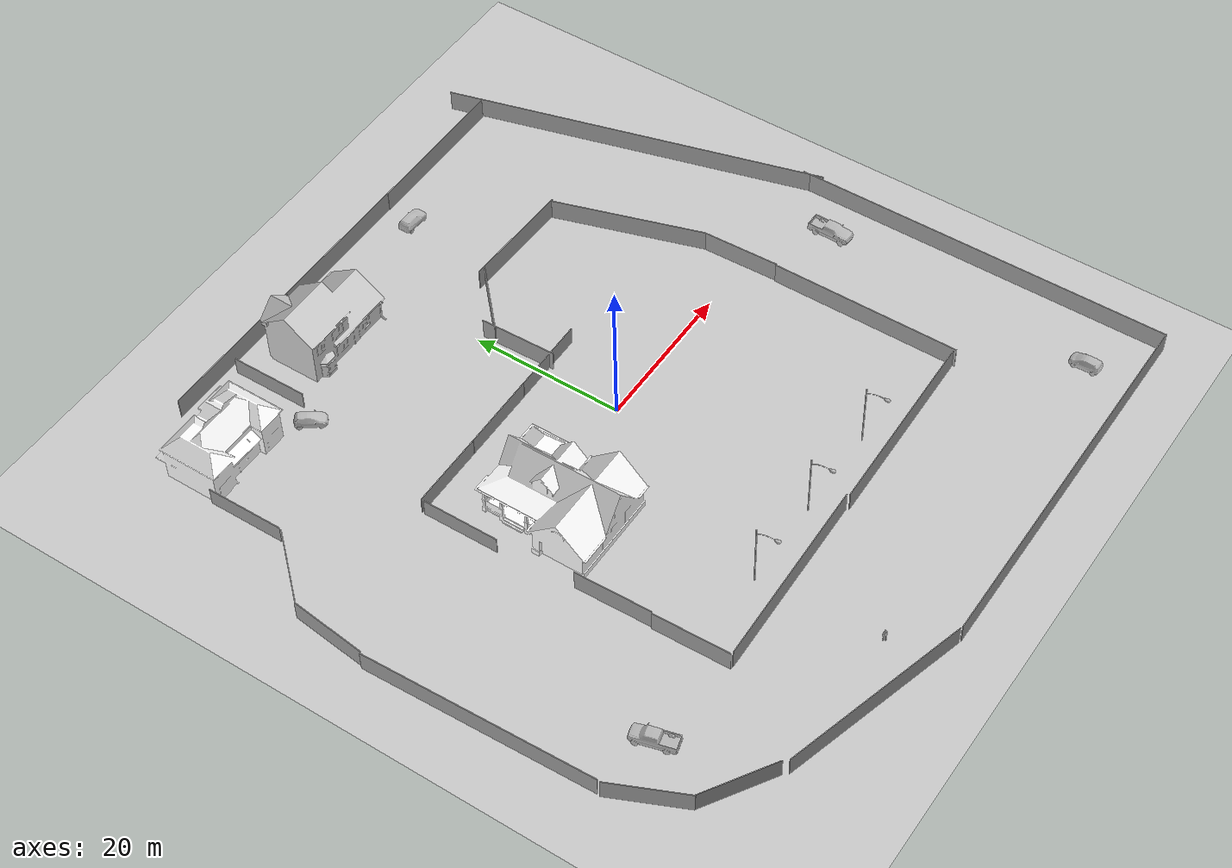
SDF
<sdf version="1.6">
 <world name="default">
  <model name="ground_plane">
   <static>1</static>
   <link name="link">
    <collision name="collision">
     <geometry><plane><normal>0 0 1</normal><size>100 100</size></plane></geometry>
     <surface>
      <contact><collide_bitmask>65535</collide_bitmask></contact>
      <friction><ode><mu>100</mu><mu2>50</mu2></ode></friction>
     </surface>
    </collision>
    <visual name="visual">
     <cast_shadows>0</cast_shadows>
     <geometry><plane><normal>0 0 1</normal><size>100 100</size></plane></geometry>
     <material>
      <script><uri>file://media/materials/scripts/gazebo.material</uri><name>Gazebo/Grey</name></script>
     </material>
    </visual>
   </link>
  </model>
  <light name="sun" type="directional">
   <pose>0 0 10 0 -0 0</pose>
   <diffuse>0.8 0.8 0.8 1</diffuse>
   <specular>0.2 0.2 0.2 1</specular>
   <attenuation>
    <range>1000</range>
    <constant>0.9</constant>
    <linear>0.01</linear>
    <quadratic>0.001</quadratic>
   </attenuation>
   <direction>-0.5 0.1 -0.9</direction>
  </light>
  <gravity>0 0 -9.8</gravity>
  <magnetic_field>6e-06 2.3e-05 -4.2e-05</magnetic_field>
  <atmosphere type="adiabatic"/>
  <physics name="default_physics" default="0" type="ode">
   <max_step_size>0.001</max_step_size>
   <real_time_factor>1</real_time_factor>
   <real_time_update_rate>1000</real_time_update_rate>
  </physics>
  <scene><ambient>0.4 0.4 0.4 1</ambient><background>0.7 0.7 0.7 1</background><shadows>1</shadows></scene>
  <audio><device>default</device></audio>
  <spherical_coordinates>
   <surface_model>EARTH_WGS84</surface_model>
   <latitude_deg>0</latitude_deg>
   <longitude_deg>0</longitude_deg>
   <elevation>0</elevation>
   <heading_deg>0</heading_deg>
  </spherical_coordinates>
  <model name="House 1">
   <static>1</static>
   <link name="link">
    <collision name="collision">
     <geometry><mesh><uri>model://house_1/meshes/house_1.dae</uri><scale>1.5 1.5 1.5</scale></mesh></geometry>
    </collision>
    <visual name="visual">
     <geometry><mesh><uri>model://house_1/meshes/house_1.dae</uri><scale>1.5 1.5 1.5</scale></mesh></geometry>
     <material>
      <script>
       <uri>model://house_1/materials/scripts</uri>
       <uri>model://house_1/materials/textures</uri>
       <name>House_1/Diffuse</name>
      </script>
      <shader type="normal_map_tangent_space"><normal_map>House_1_Normal.png</normal_map></shader>
     </material>
    </visual>
   </link>
   <pose>-15.4593 -3.01786 0 0 0 -1.56894</pose>
  </model>
  <model name="House 2">
   <static>1</static>
   <link name="link">
    <collision name="collision">
     <geometry><mesh><uri>model://house_2/meshes/house_2.dae</uri><scale>1.5 1.5 1.5</scale></mesh></geometry>
    </collision>
    <visual name="visual">
     <geometry><mesh><uri>model://house_2/meshes/house_2.dae</uri><scale>1.5 1.5 1.5</scale></mesh></geometry>
     <material>
      <script>
       <uri>model://house_2/materials/scripts</uri>
       <uri>model://house_2/materials/textures</uri>
       <uri>model://house_1/materials/textures</uri>
       <name>House_2/Diffuse</name>
      </script>
      <shader type="normal_map_tangent_space">
       <normal_map>model://house_1/materials/textures/House_1_Normal.png</normal_map>
      </shader>
     </material>
    </visual>
   </link>
   <pose>-31.041 34.0063 0 0 -0 0</pose>
  </model>
  <model name="hatchback_red">
   <static>1</static>
   <link name="link">
    <collision name="collision">
     <pose>0 0 0 0 -0 1.5708</pose>
     <geometry>
      <mesh><scale>0.0254 0.0254 0.0254</scale><uri>model://hatchback_red/meshes/hatchback.obj</uri></mesh>
     </geometry>
    </collision>
    <visual name="visual">
     <pose>0 0 0 0 -0 1.5708</pose>
     <geometry>
      <mesh><scale>0.0254 0.0254 0.0254</scale><uri>model://hatchback_red/meshes/hatchback.obj</uri></mesh>
     </geometry>
    </visual>
   </link>
   <pose>-21.1728 29.0448 0 0 0 -0.902517</pose>
  </model>
  <model name="unit_box">
   <link name="link">
    <inertial>
     <mass>1</mass>
     <inertia>
      <ixx>0.166667</ixx>
      <ixy>0</ixy>
      <ixz>0</ixz>
      <iyy>0.166667</iyy>
      <iyz>0</iyz>
      <izz>0.166667</izz>
     </inertia>
    </inertial>
    <pose>0.677495 1.60676 0.740262 0 -0 0</pose>
    <visual name="visual">
     <geometry><box><size>0.1 10 2.5</size></box></geometry>
     <material>
      <script><name>Gazebo/Grey</name><uri>file://media/materials/scripts/gazebo.material</uri></script>
      <shader type="vertex"><normal_map>__default__</normal_map></shader>
      <ambient>0.3 0.3 0.3 1</ambient>
      <diffuse>0.7 0.7 0.7 1</diffuse>
      <specular>0.01 0.01 0.01 1</specular>
      <emissive>0 0 0 1</emissive>
     </material>
    </visual>
    <collision name="collision">
     <geometry><box><size>0.1 10 2.5</size></box></geometry>
     <surface>
      <friction>
       <ode><mu>1</mu><mu2>1</mu2><fdir1>0 0 0</fdir1><slip1>0</slip1><slip2>0</slip2></ode>
       <torsional>
        <coefficient>1</coefficient>
        <patch_radius>0</patch_radius>
        <surface_radius>0</surface_radius>
        <use_patch_radius>1</use_patch_radius>
        <ode><slip>0</slip></ode>
       </torsional>
      </friction>
      <bounce><restitution_coefficient>0</restitution_coefficient><threshold>1e+06</threshold></bounce>
      <contact>
       <collide_without_contact>0</collide_without_contact>
       <collide_without_contact_bitmask>1</collide_without_contact_bitmask>
       <collide_bitmask>1</collide_bitmask>
       <ode>
        <soft_cfm>0</soft_cfm>
        <soft_erp>0.2</soft_erp>
        <kp>1e+13</kp>
        <kd>1</kd>
        <max_vel>0.01</max_vel>
        <min_depth>0</min_depth>
       </ode>
       <bullet>
        <split_impulse>1</split_impulse>
        <split_impulse_penetration_threshold>-0.01</split_impulse_penetration_threshold>
        <soft_cfm>0</soft_cfm>
        <soft_erp>0.2</soft_erp>
        <kp>1e+13</kp>
        <kd>1</kd>
       </bullet>
      </contact>
     </surface>
    </collision>
   </link>
   <link name="link_clone">
    <inertial>
     <mass>1</mass>
     <inertia>
      <ixx>0.166667</ixx>
      <ixy>0</ixy>
      <ixz>0</ixz>
      <iyy>0.166667</iyy>
      <iyz>0</iyz>
      <izz>0.166667</izz>
     </inertia>
    </inertial>
    <pose>-16.0167 -8.24232 0.740262 0 -0 0</pose>
    <visual name="visual">
     <geometry><box><size>0.1 10 2.5</size></box></geometry>
     <material>
      <script><name>Gazebo/Grey</name><uri>file://media/materials/scripts/gazebo.material</uri></script>
      <shader type="vertex"><normal_map>__default__</normal_map></shader>
      <ambient>0.3 0.3 0.3 1</ambient>
      <diffuse>0.7 0.7 0.7 1</diffuse>
      <specular>0.01 0.01 0.01 1</specular>
      <emissive>0 0 0 1</emissive>
     </material>
    </visual>
    <collision name="collision">
     <geometry><box><size>0.1 10 2.5</size></box></geometry>
     <surface>
      <friction>
       <ode><mu>1</mu><mu2>1</mu2><fdir1>0 0 0</fdir1><slip1>0</slip1><slip2>0</slip2></ode>
       <torsional>
        <coefficient>1</coefficient>
        <patch_radius>0</patch_radius>
        <surface_radius>0</surface_radius>
        <use_patch_radius>1</use_patch_radius>
        <ode><slip>0</slip></ode>
       </torsional>
      </friction>
      <bounce><restitution_coefficient>0</restitution_coefficient><threshold>1e+06</threshold></bounce>
      <contact>
       <collide_without_contact>0</collide_without_contact>
       <collide_without_contact_bitmask>1</collide_without_contact_bitmask>
       <collide_bitmask>1</collide_bitmask>
       <ode>
        <soft_cfm>0</soft_cfm>
        <soft_erp>0.2</soft_erp>
        <kp>1e+13</kp>
        <kd>1</kd>
        <max_vel>0.01</max_vel>
        <min_depth>0</min_depth>
       </ode>
       <bullet>
        <split_impulse>1</split_impulse>
        <split_impulse_penetration_threshold>-0.01</split_impulse_penetration_threshold>
        <soft_cfm>0</soft_cfm>
        <soft_erp>0.2</soft_erp>
        <kp>1e+13</kp>
        <kd>1</kd>
       </bullet>
      </contact>
     </surface>
    </collision>
   </link>
   <link name="link_clone_clone">
    <inertial>
     <mass>1</mass>
     <inertia>
      <ixx>0.166667</ixx>
      <ixy>0</ixy>
      <ixz>0</ixz>
      <iyy>0.166667</iyy>
      <iyz>0</iyz>
      <izz>0.166667</izz>
     </inertia>
    </inertial>
    <pose>-4.26052 -29.4127 0.740262 0 -0 0</pose>
    <visual name="visual">
     <geometry><box><size>0.1 10 2.5</size></box></geometry>
     <material>
      <script><name>Gazebo/Grey</name><uri>file://media/materials/scripts/gazebo.material</uri></script>
      <shader type="vertex"><normal_map>__default__</normal_map></shader>
      <ambient>0.3 0.3 0.3 1</ambient>
      <diffuse>0.7 0.7 0.7 1</diffuse>
      <specular>0.01 0.01 0.01 1</specular>
      <emissive>0 0 0 1</emissive>
     </material>
    </visual>
    <collision name="collision">
     <geometry><box><size>0.1 10 2.5</size></box></geometry>
     <surface>
      <friction>
       <ode><mu>1</mu><mu2>1</mu2><fdir1>0 0 0</fdir1><slip1>0</slip1><slip2>0</slip2></ode>
       <torsional>
        <coefficient>1</coefficient>
        <patch_radius>0</patch_radius>
        <surface_radius>0</surface_radius>
        <use_patch_radius>1</use_patch_radius>
        <ode><slip>0</slip></ode>
       </torsional>
      </friction>
      <bounce><restitution_coefficient>0</restitution_coefficient><threshold>1e+06</threshold></bounce>
      <contact>
       <collide_without_contact>0</collide_without_contact>
       <collide_without_contact_bitmask>1</collide_without_contact_bitmask>
       <collide_bitmask>1</collide_bitmask>
       <ode>
        <soft_cfm>0</soft_cfm>
        <soft_erp>0.2</soft_erp>
        <kp>1e+13</kp>
        <kd>1</kd>
        <max_vel>0.01</max_vel>
        <min_depth>0</min_depth>
       </ode>
       <bullet>
        <split_impulse>1</split_impulse>
        <split_impulse_penetration_threshold>-0.01</split_impulse_penetration_threshold>
        <soft_cfm>0</soft_cfm>
        <soft_erp>0.2</soft_erp>
        <kp>1e+13</kp>
        <kd>1</kd>
       </bullet>
      </contact>
     </surface>
    </collision>
   </link>
   <link name="link_clone_clone_0">
    <inertial>
     <mass>1</mass>
     <inertia>
      <ixx>0.166667</ixx>
      <ixy>0</ixy>
      <ixz>0</ixz>
      <iyy>0.166667</iyy>
      <iyz>0</iyz>
      <izz>0.166667</izz>
     </inertia>
    </inertial>
    <pose>0.702241 -24.0766 0.740262 -0.001448 0.002061 -1.56919</pose>
    <visual name="visual">
     <geometry><box><size>0.1 10 2.5</size></box></geometry>
     <material>
      <script><name>Gazebo/Grey</name><uri>file://media/materials/scripts/gazebo.material</uri></script>
      <shader type="vertex"><normal_map>__default__</normal_map></shader>
      <ambient>0.3 0.3 0.3 1</ambient>
      <diffuse>0.7 0.7 0.7 1</diffuse>
      <specular>0.01 0.01 0.01 1</specular>
      <emissive>0 0 0 1</emissive>
     </material>
    </visual>
    <collision name="collision">
     <geometry><box><size>0.1 10 2.5</size></box></geometry>
     <surface>
      <friction>
       <ode><mu>1</mu><mu2>1</mu2><fdir1>0 0 0</fdir1><slip1>0</slip1><slip2>0</slip2></ode>
       <torsional>
        <coefficient>1</coefficient>
        <patch_radius>0</patch_radius>
        <surface_radius>0</surface_radius>
        <use_patch_radius>1</use_patch_radius>
        <ode><slip>0</slip></ode>
       </torsional>
      </friction>
      <bounce><restitution_coefficient>0</restitution_coefficient><threshold>1e+06</threshold></bounce>
      <contact>
       <collide_without_contact>0</collide_without_contact>
       <collide_without_contact_bitmask>1</collide_without_contact_bitmask>
       <collide_bitmask>1</collide_bitmask>
       <ode>
        <soft_cfm>0</soft_cfm>
        <soft_erp>0.2</soft_erp>
        <kp>1e+13</kp>
        <kd>1</kd>
        <max_vel>0.01</max_vel>
        <min_depth>0</min_depth>
       </ode>
       <bullet>
        <split_impulse>1</split_impulse>
        <split_impulse_penetration_threshold>-0.01</split_impulse_penetration_threshold>
        <soft_cfm>0</soft_cfm>
        <soft_erp>0.2</soft_erp>
        <kp>1e+13</kp>
        <kd>1</kd>
       </bullet>
      </contact>
     </surface>
    </collision>
   </link>
   <link name="link_clone_clone_0_clone">
    <inertial>
     <mass>1</mass>
     <inertia>
      <ixx>0.166667</ixx>
      <ixy>0</ixy>
      <ixz>0</ixz>
      <iyy>0.166667</iyy>
      <iyz>0</iyz>
      <izz>0.166667</izz>
     </inertia>
    </inertial>
    <pose>10.8059 -24.0567 0.740262 0.007141 0.002047 -1.56918</pose>
    <visual name="visual">
     <geometry><box><size>0.1 10 2.5</size></box></geometry>
     <material>
      <script><name>Gazebo/Grey</name><uri>file://media/materials/scripts/gazebo.material</uri></script>
      <shader type="vertex"><normal_map>__default__</normal_map></shader>
      <ambient>0.3 0.3 0.3 1</ambient>
      <diffuse>0.7 0.7 0.7 1</diffuse>
      <specular>0.01 0.01 0.01 1</specular>
      <emissive>0 0 0 1</emissive>
     </material>
    </visual>
    <collision name="collision">
     <geometry><box><size>0.1 10 2.5</size></box></geometry>
     <surface>
      <friction>
       <ode><mu>1</mu><mu2>1</mu2><fdir1>0 0 0</fdir1><slip1>0</slip1><slip2>0</slip2></ode>
       <torsional>
        <coefficient>1</coefficient>
        <patch_radius>0</patch_radius>
        <surface_radius>0</surface_radius>
        <use_patch_radius>1</use_patch_radius>
        <ode><slip>0</slip></ode>
       </torsional>
      </friction>
      <bounce><restitution_coefficient>0</restitution_coefficient><threshold>1e+06</threshold></bounce>
      <contact>
       <collide_without_contact>0</collide_without_contact>
       <collide_without_contact_bitmask>1</collide_without_contact_bitmask>
       <collide_bitmask>1</collide_bitmask>
       <ode>
        <soft_cfm>0</soft_cfm>
        <soft_erp>0.2</soft_erp>
        <kp>1e+13</kp>
        <kd>1</kd>
        <max_vel>0.01</max_vel>
        <min_depth>0</min_depth>
       </ode>
       <bullet>
        <split_impulse>1</split_impulse>
        <split_impulse_penetration_threshold>-0.01</split_impulse_penetration_threshold>
        <soft_cfm>0</soft_cfm>
        <soft_erp>0.2</soft_erp>
        <kp>1e+13</kp>
        <kd>1</kd>
       </bullet>
      </contact>
     </surface>
    </collision>
   </link>
   <link name="link_clone_clone_0_clone_0">
    <inertial>
     <mass>1</mass>
     <inertia>
      <ixx>0.166667</ixx>
      <ixy>0</ixy>
      <ixz>0</ixz>
      <iyy>0.166667</iyy>
      <iyz>0</iyz>
      <izz>0.166667</izz>
     </inertia>
    </inertial>
    <pose>20.9566 -24.0149 0.740262 0.008761 0.002044 -1.56918</pose>
    <visual name="visual">
     <geometry><box><size>0.1 10 2.5</size></box></geometry>
     <material>
      <script><name>Gazebo/Grey</name><uri>file://media/materials/scripts/gazebo.material</uri></script>
      <shader type="vertex"><normal_map>__default__</normal_map></shader>
      <ambient>0.3 0.3 0.3 1</ambient>
      <diffuse>0.7 0.7 0.7 1</diffuse>
      <specular>0.01 0.01 0.01 1</specular>
      <emissive>0 0 0 1</emissive>
     </material>
    </visual>
    <collision name="collision">
     <geometry><box><size>0.1 10 2.5</size></box></geometry>
     <surface>
      <friction>
       <ode><mu>1</mu><mu2>1</mu2><fdir1>0 0 0</fdir1><slip1>0</slip1><slip2>0</slip2></ode>
       <torsional>
        <coefficient>1</coefficient>
        <patch_radius>0</patch_radius>
        <surface_radius>0</surface_radius>
        <use_patch_radius>1</use_patch_radius>
        <ode><slip>0</slip></ode>
       </torsional>
      </friction>
      <bounce><restitution_coefficient>0</restitution_coefficient><threshold>1e+06</threshold></bounce>
      <contact>
       <collide_without_contact>0</collide_without_contact>
       <collide_without_contact_bitmask>1</collide_without_contact_bitmask>
       <collide_bitmask>1</collide_bitmask>
       <ode>
        <soft_cfm>0</soft_cfm>
        <soft_erp>0.2</soft_erp>
        <kp>1e+13</kp>
        <kd>1</kd>
        <max_vel>0.01</max_vel>
        <min_depth>0</min_depth>
       </ode>
       <bullet>
        <split_impulse>1</split_impulse>
        <split_impulse_penetration_threshold>-0.01</split_impulse_penetration_threshold>
        <soft_cfm>0</soft_cfm>
        <soft_erp>0.2</soft_erp>
        <kp>1e+13</kp>
        <kd>1</kd>
       </bullet>
      </contact>
     </surface>
    </collision>
   </link>
   <static>1</static>
   <pose>-20.2446 34.3162 0.470073 0.006011 -5.9e-05 0.009873</pose>
  </model>
  <model name="House_3">
   <link name="link">
    <inertial>
     <inertia><ixx>1</ixx><ixy>0</ixy><ixz>0</ixz><iyy>1</iyy><iyz>0</iyz><izz>1</izz></inertia>
     <mass>1</mass>
    </inertial>
    <visual name="visual">
     <geometry><mesh><uri>model://house_3/meshes/house_3.dae</uri><scale>1.5 1.5 1.5</scale></mesh></geometry>
     <material>
      <script>
       <uri>model://house_3/materials/scripts</uri>
       <uri>model://house_3/materials/textures</uri>
       <uri>model://house_1/materials/textures</uri>
       <name>House_3/Diffuse</name>
      </script>
      <shader type="normal_map_tangent_space">
       <normal_map>model://house_1/materials/textures/House_1_Normal.png</normal_map>
      </shader>
     </material>
    </visual>
    <collision name="collision">
     <geometry>
      <mesh><uri>/home/kpit/.gazebo/models/house_3/meshes/house_3.dae</uri><scale>1.5 1.5 1.5</scale></mesh>
     </geometry>
     <surface>
      <friction>
       <ode><mu>1</mu><mu2>1</mu2><fdir1>0 0 0</fdir1><slip1>0</slip1><slip2>0</slip2></ode>
       <torsional>
        <coefficient>1</coefficient>
        <patch_radius>0</patch_radius>
        <surface_radius>0</surface_radius>
        <use_patch_radius>1</use_patch_radius>
        <ode><slip>0</slip></ode>
       </torsional>
      </friction>
      <bounce><restitution_coefficient>0</restitution_coefficient><threshold>1e+06</threshold></bounce>
      <contact>
       <collide_without_contact>0</collide_without_contact>
       <collide_without_contact_bitmask>1</collide_without_contact_bitmask>
       <collide_bitmask>1</collide_bitmask>
       <ode>
        <soft_cfm>0</soft_cfm>
        <soft_erp>0.2</soft_erp>
        <kp>1e+13</kp>
        <kd>1</kd>
        <max_vel>0.01</max_vel>
        <min_depth>0</min_depth>
       </ode>
       <bullet>
        <split_impulse>1</split_impulse>
        <split_impulse_penetration_threshold>-0.01</split_impulse_penetration_threshold>
        <soft_cfm>0</soft_cfm>
        <soft_erp>0.2</soft_erp>
        <kp>1e+13</kp>
        <kd>1</kd>
       </bullet>
      </contact>
     </surface>
    </collision>
   </link>
   <link name="link_0">
    <inertial>
     <mass>1</mass>
     <inertia>
      <ixx>0.166667</ixx>
      <ixy>0</ixy>
      <ixz>0</ixz>
      <iyy>0.166667</iyy>
      <iyz>0</iyz>
      <izz>0.166667</izz>
     </inertia>
    </inertial>
    <pose>27.4713 -84.731 1.24847 0 -0 0</pose>
    <visual name="visual">
     <geometry><box><size>50 0.1 3</size></box></geometry>
     <material>
      <lighting>1</lighting>
      <script><uri>file://media/materials/scripts/gazebo.material</uri><name>Gazebo/Grey</name></script>
      <shader type="vertex"><normal_map>__default__</normal_map></shader>
      <ambient>0.3 0.3 0.3 1</ambient>
      <diffuse>0.7 0.7 0.7 1</diffuse>
      <specular>0.01 0.01 0.01 1</specular>
      <emissive>0 0 0 1</emissive>
     </material>
    </visual>
    <collision name="collision">
     <geometry><box><size>50 0.1 3</size></box></geometry>
     <surface>
      <friction>
       <ode><mu>1</mu><mu2>1</mu2><fdir1>0 0 0</fdir1><slip1>0</slip1><slip2>0</slip2></ode>
       <torsional>
        <coefficient>1</coefficient>
        <patch_radius>0</patch_radius>
        <surface_radius>0</surface_radius>
        <use_patch_radius>1</use_patch_radius>
        <ode><slip>0</slip></ode>
       </torsional>
      </friction>
      <bounce><restitution_coefficient>0</restitution_coefficient><threshold>1e+06</threshold></bounce>
      <contact>
       <collide_without_contact>0</collide_without_contact>
       <collide_without_contact_bitmask>1</collide_without_contact_bitmask>
       <collide_bitmask>1</collide_bitmask>
       <ode>
        <soft_cfm>0</soft_cfm>
        <soft_erp>0.2</soft_erp>
        <kp>1e+13</kp>
        <kd>1</kd>
        <max_vel>0.01</max_vel>
        <min_depth>0</min_depth>
       </ode>
       <bullet>
        <split_impulse>1</split_impulse>
        <split_impulse_penetration_threshold>-0.01</split_impulse_penetration_threshold>
        <soft_cfm>0</soft_cfm>
        <soft_erp>0.2</soft_erp>
        <kp>1e+13</kp>
        <kd>1</kd>
       </bullet>
      </contact>
     </surface>
    </collision>
   </link>
   <link name="link_0_clone">
    <inertial>
     <mass>1</mass>
     <inertia>
      <ixx>0.166667</ixx>
      <ixy>0</ixy>
      <ixz>0</ixz>
      <iyy>0.166667</iyy>
      <iyz>0</iyz>
      <izz>0.166667</izz>
     </inertia>
    </inertial>
    <pose>52.241 -59.7234 1.24847 0 -0 1.57244</pose>
    <visual name="visual">
     <geometry><box><size>50 0.1 3</size></box></geometry>
     <material>
      <lighting>1</lighting>
      <script><uri>file://media/materials/scripts/gazebo.material</uri><name>Gazebo/Grey</name></script>
      <shader type="vertex"><normal_map>__default__</normal_map></shader>
      <ambient>0.3 0.3 0.3 1</ambient>
      <diffuse>0.7 0.7 0.7 1</diffuse>
      <specular>0.01 0.01 0.01 1</specular>
      <emissive>0 0 0 1</emissive>
     </material>
    </visual>
    <collision name="collision">
     <geometry><box><size>50 0.1 3</size></box></geometry>
     <surface>
      <friction>
       <ode><mu>1</mu><mu2>1</mu2><fdir1>0 0 0</fdir1><slip1>0</slip1><slip2>0</slip2></ode>
       <torsional>
        <coefficient>1</coefficient>
        <patch_radius>0</patch_radius>
        <surface_radius>0</surface_radius>
        <use_patch_radius>1</use_patch_radius>
        <ode><slip>0</slip></ode>
       </torsional>
      </friction>
      <bounce><restitution_coefficient>0</restitution_coefficient><threshold>1e+06</threshold></bounce>
      <contact>
       <collide_without_contact>0</collide_without_contact>
       <collide_without_contact_bitmask>1</collide_without_contact_bitmask>
       <collide_bitmask>1</collide_bitmask>
       <ode>
        <soft_cfm>0</soft_cfm>
        <soft_erp>0.2</soft_erp>
        <kp>1e+13</kp>
        <kd>1</kd>
        <max_vel>0.01</max_vel>
        <min_depth>0</min_depth>
       </ode>
       <bullet>
        <split_impulse>1</split_impulse>
        <split_impulse_penetration_threshold>-0.01</split_impulse_penetration_threshold>
        <soft_cfm>0</soft_cfm>
        <soft_erp>0.2</soft_erp>
        <kp>1e+13</kp>
        <kd>1</kd>
       </bullet>
      </contact>
     </surface>
    </collision>
   </link>
   <link name="link_0_clone_clone">
    <inertial>
     <mass>1</mass>
     <inertia>
      <ixx>0.166667</ixx>
      <ixy>0</ixy>
      <ixz>0</ixz>
      <iyy>0.166667</iyy>
      <iyz>0</iyz>
      <izz>0.166667</izz>
     </inertia>
    </inertial>
    <pose>46.1337 -13.1709 1.24847 0 -0 1.83448</pose>
    <visual name="visual">
     <geometry><box><size>50 0.1 3</size></box></geometry>
     <material>
      <lighting>1</lighting>
      <script><uri>file://media/materials/scripts/gazebo.material</uri><name>Gazebo/Grey</name></script>
      <shader type="vertex"><normal_map>__default__</normal_map></shader>
      <ambient>0.3 0.3 0.3 1</ambient>
      <diffuse>0.7 0.7 0.7 1</diffuse>
      <specular>0.01 0.01 0.01 1</specular>
      <emissive>0 0 0 1</emissive>
     </material>
    </visual>
    <collision name="collision">
     <geometry><box><size>50 0.1 3</size></box></geometry>
     <surface>
      <friction>
       <ode><mu>1</mu><mu2>1</mu2><fdir1>0 0 0</fdir1><slip1>0</slip1><slip2>0</slip2></ode>
       <torsional>
        <coefficient>1</coefficient>
        <patch_radius>0</patch_radius>
        <surface_radius>0</surface_radius>
        <use_patch_radius>1</use_patch_radius>
        <ode><slip>0</slip></ode>
       </torsional>
      </friction>
      <bounce><restitution_coefficient>0</restitution_coefficient><threshold>1e+06</threshold></bounce>
      <contact>
       <collide_without_contact>0</collide_without_contact>
       <collide_without_contact_bitmask>1</collide_without_contact_bitmask>
       <collide_bitmask>1</collide_bitmask>
       <ode>
        <soft_cfm>0</soft_cfm>
        <soft_erp>0.2</soft_erp>
        <kp>1e+13</kp>
        <kd>1</kd>
        <max_vel>0.01</max_vel>
        <min_depth>0</min_depth>
       </ode>
       <bullet>
        <split_impulse>1</split_impulse>
        <split_impulse_penetration_threshold>-0.01</split_impulse_penetration_threshold>
        <soft_cfm>0</soft_cfm>
        <soft_erp>0.2</soft_erp>
        <kp>1e+13</kp>
        <kd>1</kd>
       </bullet>
      </contact>
     </surface>
    </collision>
   </link>
   <link name="link_0_clone_clone_clone">
    <inertial>
     <mass>1</mass>
     <inertia>
      <ixx>0.166667</ixx>
      <ixy>0</ixy>
      <ixz>0</ixz>
      <iyy>0.166667</iyy>
      <iyz>0</iyz>
      <izz>0.166667</izz>
     </inertia>
    </inertial>
    <pose>33.5876 -20.7243 1.24847 0 -0 1.87008</pose>
    <visual name="visual">
     <geometry><box><size>20 0.1 3</size></box></geometry>
     <material>
      <lighting>1</lighting>
      <script><uri>file://media/materials/scripts/gazebo.material</uri><name>Gazebo/Grey</name></script>
      <shader type="vertex"><normal_map>__default__</normal_map></shader>
      <ambient>0.3 0.3 0.3 1</ambient>
      <diffuse>0.7 0.7 0.7 1</diffuse>
      <specular>0.01 0.01 0.01 1</specular>
      <emissive>0 0 0 1</emissive>
     </material>
    </visual>
    <collision name="collision">
     <geometry><box><size>20 0.1 3</size></box></geometry>
     <surface>
      <friction>
       <ode><mu>1</mu><mu2>1</mu2><fdir1>0 0 0</fdir1><slip1>0</slip1><slip2>0</slip2></ode>
       <torsional>
        <coefficient>1</coefficient>
        <patch_radius>0</patch_radius>
        <surface_radius>0</surface_radius>
        <use_patch_radius>1</use_patch_radius>
        <ode><slip>0</slip></ode>
       </torsional>
      </friction>
      <bounce><restitution_coefficient>0</restitution_coefficient><threshold>1e+06</threshold></bounce>
      <contact>
       <collide_without_contact>0</collide_without_contact>
       <collide_without_contact_bitmask>1</collide_without_contact_bitmask>
       <collide_bitmask>1</collide_bitmask>
       <ode>
        <soft_cfm>0</soft_cfm>
        <soft_erp>0.2</soft_erp>
        <kp>1e+13</kp>
        <kd>1</kd>
        <max_vel>0.01</max_vel>
        <min_depth>0</min_depth>
       </ode>
       <bullet>
        <split_impulse>1</split_impulse>
        <split_impulse_penetration_threshold>-0.01</split_impulse_penetration_threshold>
        <soft_cfm>0</soft_cfm>
        <soft_erp>0.2</soft_erp>
        <kp>1e+13</kp>
        <kd>1</kd>
       </bullet>
      </contact>
     </surface>
    </collision>
   </link>
   <link name="link_0_clone_clone_clone_clone">
    <inertial>
     <mass>1</mass>
     <inertia>
      <ixx>0.166667</ixx>
      <ixy>0</ixy>
      <ixz>0</ixz>
      <iyy>0.166667</iyy>
      <iyz>0</iyz>
      <izz>0.166667</izz>
     </inertia>
    </inertial>
    <pose>36.6159 -52.6479 1.24847 0 -0 1.57014</pose>
    <visual name="visual">
     <geometry><box><size>25 0.1 3</size></box></geometry>
     <material>
      <lighting>1</lighting>
      <script><uri>file://media/materials/scripts/gazebo.material</uri><name>Gazebo/Grey</name></script>
      <shader type="vertex"><normal_map>__default__</normal_map></shader>
      <ambient>0.3 0.3 0.3 1</ambient>
      <diffuse>0.7 0.7 0.7 1</diffuse>
      <specular>0.01 0.01 0.01 1</specular>
      <emissive>0 0 0 1</emissive>
     </material>
    </visual>
    <collision name="collision">
     <geometry><box><size>25 0.1 3</size></box></geometry>
     <surface>
      <friction>
       <ode><mu>1</mu><mu2>1</mu2><fdir1>0 0 0</fdir1><slip1>0</slip1><slip2>0</slip2></ode>
       <torsional>
        <coefficient>1</coefficient>
        <patch_radius>0</patch_radius>
        <surface_radius>0</surface_radius>
        <use_patch_radius>1</use_patch_radius>
        <ode><slip>0</slip></ode>
       </torsional>
      </friction>
      <bounce><restitution_coefficient>0</restitution_coefficient><threshold>1e+06</threshold></bounce>
      <contact>
       <collide_without_contact>0</collide_without_contact>
       <collide_without_contact_bitmask>1</collide_without_contact_bitmask>
       <collide_bitmask>1</collide_bitmask>
       <ode>
        <soft_cfm>0</soft_cfm>
        <soft_erp>0.2</soft_erp>
        <kp>1e+13</kp>
        <kd>1</kd>
        <max_vel>0.01</max_vel>
        <min_depth>0</min_depth>
       </ode>
       <bullet>
        <split_impulse>1</split_impulse>
        <split_impulse_penetration_threshold>-0.01</split_impulse_penetration_threshold>
        <soft_cfm>0</soft_cfm>
        <soft_erp>0.2</soft_erp>
        <kp>1e+13</kp>
        <kd>1</kd>
       </bullet>
      </contact>
     </surface>
    </collision>
   </link>
   <link name="link_0_clone_clone_clone_clone_0_clone">
    <inertial>
     <mass>1</mass>
     <inertia>
      <ixx>0.166667</ixx>
      <ixy>0</ixy>
      <ixz>0</ixz>
      <iyy>0.166667</iyy>
      <iyz>0</iyz>
      <izz>0.166667</izz>
     </inertia>
    </inertial>
    <pose>30.5119 6.6857 1.24847 -0 -0 -3.13692</pose>
    <visual name="visual">
     <geometry><box><size>20 0.1 3</size></box></geometry>
     <material>
      <lighting>1</lighting>
      <script><uri>file://media/materials/scripts/gazebo.material</uri><name>Gazebo/Grey</name></script>
      <shader type="vertex"><normal_map>__default__</normal_map></shader>
      <ambient>0.3 0.3 0.3 1</ambient>
      <diffuse>0.7 0.7 0.7 1</diffuse>
      <specular>0.01 0.01 0.01 1</specular>
      <emissive>0 0 0 1</emissive>
     </material>
    </visual>
    <collision name="collision">
     <geometry><box><size>20 0.1 3</size></box></geometry>
     <surface>
      <friction>
       <ode><mu>1</mu><mu2>1</mu2><fdir1>0 0 0</fdir1><slip1>0</slip1><slip2>0</slip2></ode>
       <torsional>
        <coefficient>1</coefficient>
        <patch_radius>0</patch_radius>
        <surface_radius>0</surface_radius>
        <use_patch_radius>1</use_patch_radius>
        <ode><slip>0</slip></ode>
       </torsional>
      </friction>
      <bounce><restitution_coefficient>0</restitution_coefficient><threshold>1e+06</threshold></bounce>
      <contact>
       <collide_without_contact>0</collide_without_contact>
       <collide_without_contact_bitmask>1</collide_without_contact_bitmask>
       <collide_bitmask>1</collide_bitmask>
       <ode>
        <soft_cfm>0</soft_cfm>
        <soft_erp>0.2</soft_erp>
        <kp>1e+13</kp>
        <kd>1</kd>
        <max_vel>0.01</max_vel>
        <min_depth>0</min_depth>
       </ode>
       <bullet>
        <split_impulse>1</split_impulse>
        <split_impulse_penetration_threshold>-0.01</split_impulse_penetration_threshold>
        <soft_cfm>0</soft_cfm>
        <soft_erp>0.2</soft_erp>
        <kp>1e+13</kp>
        <kd>1</kd>
       </bullet>
      </contact>
     </surface>
    </collision>
   </link>
   <link name="link_0_clone_clone_clone_clone_0_clone_0">
    <inertial>
     <mass>1</mass>
     <inertia>
      <ixx>0.166667</ixx>
      <ixy>0</ixy>
      <ixz>0</ixz>
      <iyy>0.166667</iyy>
      <iyz>0</iyz>
      <izz>0.166667</izz>
     </inertia>
    </inertial>
    <pose>10.5116 6.64563 1.24847 -0 -0 -3.13692</pose>
    <visual name="visual">
     <geometry><box><size>20 0.1 3</size></box></geometry>
     <material>
      <lighting>1</lighting>
      <script><uri>file://media/materials/scripts/gazebo.material</uri><name>Gazebo/Grey</name></script>
      <shader type="vertex"><normal_map>__default__</normal_map></shader>
      <ambient>0.3 0.3 0.3 1</ambient>
      <diffuse>0.7 0.7 0.7 1</diffuse>
      <specular>0.01 0.01 0.01 1</specular>
      <emissive>0 0 0 1</emissive>
     </material>
    </visual>
    <collision name="collision">
     <geometry><box><size>20 0.1 3</size></box></geometry>
     <surface>
      <friction>
       <ode><mu>1</mu><mu2>1</mu2><fdir1>0 0 0</fdir1><slip1>0</slip1><slip2>0</slip2></ode>
       <torsional>
        <coefficient>1</coefficient>
        <patch_radius>0</patch_radius>
        <surface_radius>0</surface_radius>
        <use_patch_radius>1</use_patch_radius>
        <ode><slip>0</slip></ode>
       </torsional>
      </friction>
      <bounce><restitution_coefficient>0</restitution_coefficient><threshold>1e+06</threshold></bounce>
      <contact>
       <collide_without_contact>0</collide_without_contact>
       <collide_without_contact_bitmask>1</collide_without_contact_bitmask>
       <collide_bitmask>1</collide_bitmask>
       <ode>
        <soft_cfm>0</soft_cfm>
        <soft_erp>0.2</soft_erp>
        <kp>1e+13</kp>
        <kd>1</kd>
        <max_vel>0.01</max_vel>
        <min_depth>0</min_depth>
       </ode>
       <bullet>
        <split_impulse>1</split_impulse>
        <split_impulse_penetration_threshold>-0.01</split_impulse_penetration_threshold>
        <soft_cfm>0</soft_cfm>
        <soft_erp>0.2</soft_erp>
        <kp>1e+13</kp>
        <kd>1</kd>
       </bullet>
      </contact>
     </surface>
    </collision>
   </link>
   <link name="link_0_clone_clone_clone_clone_0_clone_1">
    <inertial>
     <mass>1</mass>
     <inertia>
      <ixx>0.166667</ixx>
      <ixy>0</ixy>
      <ixz>0</ixz>
      <iyy>0.166667</iyy>
      <iyz>0</iyz>
      <izz>0.166667</izz>
     </inertia>
    </inertial>
    <pose>-9.52792 6.55994 1.24847 -0 -0 -3.13692</pose>
    <visual name="visual">
     <geometry><box><size>20 0.1 3</size></box></geometry>
     <material>
      <lighting>1</lighting>
      <script><uri>file://media/materials/scripts/gazebo.material</uri><name>Gazebo/Grey</name></script>
      <shader type="vertex"><normal_map>__default__</normal_map></shader>
      <ambient>0.3 0.3 0.3 1</ambient>
      <diffuse>0.7 0.7 0.7 1</diffuse>
      <specular>0.01 0.01 0.01 1</specular>
      <emissive>0 0 0 1</emissive>
     </material>
    </visual>
    <collision name="collision">
     <geometry><box><size>20 0.1 3</size></box></geometry>
     <surface>
      <friction>
       <ode><mu>1</mu><mu2>1</mu2><fdir1>0 0 0</fdir1><slip1>0</slip1><slip2>0</slip2></ode>
       <torsional>
        <coefficient>1</coefficient>
        <patch_radius>0</patch_radius>
        <surface_radius>0</surface_radius>
        <use_patch_radius>1</use_patch_radius>
        <ode><slip>0</slip></ode>
       </torsional>
      </friction>
      <bounce><restitution_coefficient>0</restitution_coefficient><threshold>1e+06</threshold></bounce>
      <contact>
       <collide_without_contact>0</collide_without_contact>
       <collide_without_contact_bitmask>1</collide_without_contact_bitmask>
       <collide_bitmask>1</collide_bitmask>
       <ode>
        <soft_cfm>0</soft_cfm>
        <soft_erp>0.2</soft_erp>
        <kp>1e+13</kp>
        <kd>1</kd>
        <max_vel>0.01</max_vel>
        <min_depth>0</min_depth>
       </ode>
       <bullet>
        <split_impulse>1</split_impulse>
        <split_impulse_penetration_threshold>-0.01</split_impulse_penetration_threshold>
        <soft_cfm>0</soft_cfm>
        <soft_erp>0.2</soft_erp>
        <kp>1e+13</kp>
        <kd>1</kd>
       </bullet>
      </contact>
     </surface>
    </collision>
   </link>
   <link name="link_0_clone_clone_clone_clone_0_clone_1_clone">
    <inertial>
     <mass>1</mass>
     <inertia>
      <ixx>0.166667</ixx>
      <ixy>0</ixy>
      <ixz>0</ixz>
      <iyy>0.166667</iyy>
      <iyz>0</iyz>
      <izz>0.166667</izz>
     </inertia>
    </inertial>
    <pose>-30.8832 -18.8526 1.24847 -0 -0 -2.31387</pose>
    <visual name="visual">
     <geometry><box><size>10 0.1 3</size></box></geometry>
     <material>
      <lighting>1</lighting>
      <script><uri>file://media/materials/scripts/gazebo.material</uri><name>Gazebo/Grey</name></script>
      <shader type="vertex"><normal_map>__default__</normal_map></shader>
      <ambient>0.3 0.3 0.3 1</ambient>
      <diffuse>0.7 0.7 0.7 1</diffuse>
      <specular>0.01 0.01 0.01 1</specular>
      <emissive>0 0 0 1</emissive>
     </material>
    </visual>
    <collision name="collision">
     <geometry><box><size>10 0.1 3</size></box></geometry>
     <surface>
      <friction>
       <ode><mu>1</mu><mu2>1</mu2><fdir1>0 0 0</fdir1><slip1>0</slip1><slip2>0</slip2></ode>
       <torsional>
        <coefficient>1</coefficient>
        <patch_radius>0</patch_radius>
        <surface_radius>0</surface_radius>
        <use_patch_radius>1</use_patch_radius>
        <ode><slip>0</slip></ode>
       </torsional>
      </friction>
      <bounce><restitution_coefficient>0</restitution_coefficient><threshold>1e+06</threshold></bounce>
      <contact>
       <collide_without_contact>0</collide_without_contact>
       <collide_without_contact_bitmask>1</collide_without_contact_bitmask>
       <collide_bitmask>1</collide_bitmask>
       <ode>
        <soft_cfm>0</soft_cfm>
        <soft_erp>0.2</soft_erp>
        <kp>1e+13</kp>
        <kd>1</kd>
        <max_vel>0.01</max_vel>
        <min_depth>0</min_depth>
       </ode>
       <bullet>
        <split_impulse>1</split_impulse>
        <split_impulse_penetration_threshold>-0.01</split_impulse_penetration_threshold>
        <soft_cfm>0</soft_cfm>
        <soft_erp>0.2</soft_erp>
        <kp>1e+13</kp>
        <kd>1</kd>
       </bullet>
      </contact>
     </surface>
    </collision>
   </link>
   <link name="link_0_clone_clone_clone_clone_0_clone_1_clone_clone">
    <inertial>
     <mass>1</mass>
     <inertia>
      <ixx>0.166667</ixx>
      <ixy>0</ixy>
      <ixz>0</ixz>
      <iyy>0.166667</iyy>
      <iyz>0</iyz>
      <izz>0.166667</izz>
     </inertia>
    </inertial>
    <pose>-34.9276 -27.509 1.24847 0 -0 -1.68597</pose>
    <visual name="visual">
     <geometry><box><size>10 0.1 3</size></box></geometry>
     <material>
      <lighting>1</lighting>
      <script><uri>file://media/materials/scripts/gazebo.material</uri><name>Gazebo/Grey</name></script>
      <shader type="vertex"><normal_map>__default__</normal_map></shader>
      <ambient>0.3 0.3 0.3 1</ambient>
      <diffuse>0.7 0.7 0.7 1</diffuse>
      <specular>0.01 0.01 0.01 1</specular>
      <emissive>0 0 0 1</emissive>
     </material>
    </visual>
    <collision name="collision">
     <geometry><box><size>10 0.1 3</size></box></geometry>
     <surface>
      <friction>
       <ode><mu>1</mu><mu2>1</mu2><fdir1>0 0 0</fdir1><slip1>0</slip1><slip2>0</slip2></ode>
       <torsional>
        <coefficient>1</coefficient>
        <patch_radius>0</patch_radius>
        <surface_radius>0</surface_radius>
        <use_patch_radius>1</use_patch_radius>
        <ode><slip>0</slip></ode>
       </torsional>
      </friction>
      <bounce><restitution_coefficient>0</restitution_coefficient><threshold>1e+06</threshold></bounce>
      <contact>
       <collide_without_contact>0</collide_without_contact>
       <collide_without_contact_bitmask>1</collide_without_contact_bitmask>
       <collide_bitmask>1</collide_bitmask>
       <ode>
        <soft_cfm>0</soft_cfm>
        <soft_erp>0.2</soft_erp>
        <kp>1e+13</kp>
        <kd>1</kd>
        <max_vel>0.01</max_vel>
        <min_depth>0</min_depth>
       </ode>
       <bullet>
        <split_impulse>1</split_impulse>
        <split_impulse_penetration_threshold>-0.01</split_impulse_penetration_threshold>
        <soft_cfm>0</soft_cfm>
        <soft_erp>0.2</soft_erp>
        <kp>1e+13</kp>
        <kd>1</kd>
       </bullet>
      </contact>
     </surface>
    </collision>
   </link>
   <link name="link_0_clone_clone_clone_clone_0_clone_1_clone_clone_clone">
    <inertial>
     <mass>1</mass>
     <inertia>
      <ixx>0.166667</ixx>
      <ixy>0</ixy>
      <ixz>0</ixz>
      <iyy>0.166667</iyy>
      <iyz>0</iyz>
      <izz>0.166667</izz>
     </inertia>
    </inertial>
    <pose>-35.2166 -47.4695 1.24847 0 0 -1.53676</pose>
    <visual name="visual">
     <geometry><box><size>30 0.1 3</size></box></geometry>
     <material>
      <lighting>1</lighting>
      <script><uri>file://media/materials/scripts/gazebo.material</uri><name>Gazebo/Grey</name></script>
      <shader type="vertex"><normal_map>__default__</normal_map></shader>
      <ambient>0.3 0.3 0.3 1</ambient>
      <diffuse>0.7 0.7 0.7 1</diffuse>
      <specular>0.01 0.01 0.01 1</specular>
      <emissive>0 0 0 1</emissive>
     </material>
    </visual>
    <collision name="collision">
     <geometry><box><size>30 0.1 3</size></box></geometry>
     <surface>
      <friction>
       <ode><mu>1</mu><mu2>1</mu2><fdir1>0 0 0</fdir1><slip1>0</slip1><slip2>0</slip2></ode>
       <torsional>
        <coefficient>1</coefficient>
        <patch_radius>0</patch_radius>
        <surface_radius>0</surface_radius>
        <use_patch_radius>1</use_patch_radius>
        <ode><slip>0</slip></ode>
       </torsional>
      </friction>
      <bounce><restitution_coefficient>0</restitution_coefficient><threshold>1e+06</threshold></bounce>
      <contact>
       <collide_without_contact>0</collide_without_contact>
       <collide_without_contact_bitmask>1</collide_without_contact_bitmask>
       <collide_bitmask>1</collide_bitmask>
       <ode>
        <soft_cfm>0</soft_cfm>
        <soft_erp>0.2</soft_erp>
        <kp>1e+13</kp>
        <kd>1</kd>
        <max_vel>0.01</max_vel>
        <min_depth>0</min_depth>
       </ode>
       <bullet>
        <split_impulse>1</split_impulse>
        <split_impulse_penetration_threshold>-0.01</split_impulse_penetration_threshold>
        <soft_cfm>0</soft_cfm>
        <soft_erp>0.2</soft_erp>
        <kp>1e+13</kp>
        <kd>1</kd>
       </bullet>
      </contact>
     </surface>
    </collision>
   </link>
   <link name="link_0_clone_clone_clone_clone_0_clone_1_clone_clone_clone_0">
    <inertial>
     <mass>1</mass>
     <inertia>
      <ixx>0.166667</ixx>
      <ixy>0</ixy>
      <ixz>0</ixz>
      <iyy>0.166667</iyy>
      <iyz>0</iyz>
      <izz>0.166667</izz>
     </inertia>
    </inertial>
    <pose>-32.7782 -67.3476 1.24847 0 -0 -1.15434</pose>
    <visual name="visual">
     <geometry><box><size>10 0.1 3</size></box></geometry>
     <material>
      <lighting>1</lighting>
      <script><uri>file://media/materials/scripts/gazebo.material</uri><name>Gazebo/Grey</name></script>
      <shader type="vertex"><normal_map>__default__</normal_map></shader>
      <ambient>0.3 0.3 0.3 1</ambient>
      <diffuse>0.7 0.7 0.7 1</diffuse>
      <specular>0.01 0.01 0.01 1</specular>
      <emissive>0 0 0 1</emissive>
     </material>
    </visual>
    <collision name="collision">
     <geometry><box><size>10 0.1 3</size></box></geometry>
     <surface>
      <friction>
       <ode><mu>1</mu><mu2>1</mu2><fdir1>0 0 0</fdir1><slip1>0</slip1><slip2>0</slip2></ode>
       <torsional>
        <coefficient>1</coefficient>
        <patch_radius>0</patch_radius>
        <surface_radius>0</surface_radius>
        <use_patch_radius>1</use_patch_radius>
        <ode><slip>0</slip></ode>
       </torsional>
      </friction>
      <bounce><restitution_coefficient>0</restitution_coefficient><threshold>1e+06</threshold></bounce>
      <contact>
       <collide_without_contact>0</collide_without_contact>
       <collide_without_contact_bitmask>1</collide_without_contact_bitmask>
       <collide_bitmask>1</collide_bitmask>
       <ode>
        <soft_cfm>0</soft_cfm>
        <soft_erp>0.2</soft_erp>
        <kp>1e+13</kp>
        <kd>1</kd>
        <max_vel>0.01</max_vel>
        <min_depth>0</min_depth>
       </ode>
       <bullet>
        <split_impulse>1</split_impulse>
        <split_impulse_penetration_threshold>-0.01</split_impulse_penetration_threshold>
        <soft_cfm>0</soft_cfm>
        <soft_erp>0.2</soft_erp>
        <kp>1e+13</kp>
        <kd>1</kd>
       </bullet>
      </contact>
     </surface>
    </collision>
   </link>
   <link name="link_0_clone_clone_clone_clone_0_clone_1_clone_clone_clone_0_clone">
    <inertial>
     <mass>1</mass>
     <inertia>
      <ixx>0.166667</ixx>
      <ixy>0</ixy>
      <ixz>0</ixz>
      <iyy>0.166667</iyy>
      <iyz>0</iyz>
      <izz>0.166667</izz>
     </inertia>
    </inertial>
    <pose>-26.5795 -74.5086 1.24847 0 0 -0.56512</pose>
    <visual name="visual">
     <geometry><box><size>10 0.1 3</size></box></geometry>
     <material>
      <lighting>1</lighting>
      <script><uri>file://media/materials/scripts/gazebo.material</uri><name>Gazebo/Grey</name></script>
      <shader type="vertex"><normal_map>__default__</normal_map></shader>
      <ambient>0.3 0.3 0.3 1</ambient>
      <diffuse>0.7 0.7 0.7 1</diffuse>
      <specular>0.01 0.01 0.01 1</specular>
      <emissive>0 0 0 1</emissive>
     </material>
    </visual>
    <collision name="collision">
     <geometry><box><size>10 0.1 3</size></box></geometry>
     <surface>
      <friction>
       <ode><mu>1</mu><mu2>1</mu2><fdir1>0 0 0</fdir1><slip1>0</slip1><slip2>0</slip2></ode>
       <torsional>
        <coefficient>1</coefficient>
        <patch_radius>0</patch_radius>
        <surface_radius>0</surface_radius>
        <use_patch_radius>1</use_patch_radius>
        <ode><slip>0</slip></ode>
       </torsional>
      </friction>
      <bounce><restitution_coefficient>0</restitution_coefficient><threshold>1e+06</threshold></bounce>
      <contact>
       <collide_without_contact>0</collide_without_contact>
       <collide_without_contact_bitmask>1</collide_without_contact_bitmask>
       <collide_bitmask>1</collide_bitmask>
       <ode>
        <soft_cfm>0</soft_cfm>
        <soft_erp>0.2</soft_erp>
        <kp>1e+13</kp>
        <kd>1</kd>
        <max_vel>0.01</max_vel>
        <min_depth>0</min_depth>
       </ode>
       <bullet>
        <split_impulse>1</split_impulse>
        <split_impulse_penetration_threshold>-0.01</split_impulse_penetration_threshold>
        <soft_cfm>0</soft_cfm>
        <soft_erp>0.2</soft_erp>
        <kp>1e+13</kp>
        <kd>1</kd>
       </bullet>
      </contact>
     </surface>
    </collision>
   </link>
   <link name="link_0_clone_clone_clone_clone_0_clone_1_clone_clone_clone_0_clone_clone">
    <inertial>
     <mass>1</mass>
     <inertia>
      <ixx>0.166667</ixx>
      <ixy>0</ixy>
      <ixz>0</ixz>
      <iyy>0.166667</iyy>
      <iyz>0</iyz>
      <izz>0.166667</izz>
     </inertia>
    </inertial>
    <pose>36.6261 -35.2011 1.24847 0 -0 1.60144</pose>
    <visual name="visual">
     <geometry><box><size>10 0.1 3</size></box></geometry>
     <material>
      <lighting>1</lighting>
      <script><uri>file://media/materials/scripts/gazebo.material</uri><name>Gazebo/Grey</name></script>
      <shader type="vertex"><normal_map>__default__</normal_map></shader>
      <ambient>0.3 0.3 0.3 1</ambient>
      <diffuse>0.7 0.7 0.7 1</diffuse>
      <specular>0.01 0.01 0.01 1</specular>
      <emissive>0 0 0 1</emissive>
     </material>
    </visual>
    <collision name="collision">
     <geometry><box><size>10 0.1 3</size></box></geometry>
     <surface>
      <friction>
       <ode><mu>1</mu><mu2>1</mu2><fdir1>0 0 0</fdir1><slip1>0</slip1><slip2>0</slip2></ode>
       <torsional>
        <coefficient>1</coefficient>
        <patch_radius>0</patch_radius>
        <surface_radius>0</surface_radius>
        <use_patch_radius>1</use_patch_radius>
        <ode><slip>0</slip></ode>
       </torsional>
      </friction>
      <bounce><restitution_coefficient>0</restitution_coefficient><threshold>1e+06</threshold></bounce>
      <contact>
       <collide_without_contact>0</collide_without_contact>
       <collide_without_contact_bitmask>1</collide_without_contact_bitmask>
       <collide_bitmask>1</collide_bitmask>
       <ode>
        <soft_cfm>0</soft_cfm>
        <soft_erp>0.2</soft_erp>
        <kp>1e+13</kp>
        <kd>1</kd>
        <max_vel>0.01</max_vel>
        <min_depth>0</min_depth>
       </ode>
       <bullet>
        <split_impulse>1</split_impulse>
        <split_impulse_penetration_threshold>-0.01</split_impulse_penetration_threshold>
        <soft_cfm>0</soft_cfm>
        <soft_erp>0.2</soft_erp>
        <kp>1e+13</kp>
        <kd>1</kd>
       </bullet>
      </contact>
     </surface>
    </collision>
   </link>
   <link name="link_0_clone_clone_clone_clone_0_clone_1_clone_clone_clone_0_clone_clone_0">
    <inertial>
     <mass>1</mass>
     <inertia>
      <ixx>0.166667</ixx>
      <ixy>0</ixy>
      <ixz>0</ixz>
      <iyy>0.166667</iyy>
      <iyz>0</iyz>
      <izz>0.166667</izz>
     </inertia>
    </inertial>
    <pose>-14.2688 -60.7697 1.24847 0 -0 -1.54437</pose>
    <visual name="visual">
     <geometry><box><size>10 0.1 3</size></box></geometry>
     <material>
      <lighting>1</lighting>
      <script><uri>file://media/materials/scripts/gazebo.material</uri><name>Gazebo/Grey</name></script>
      <shader type="vertex"><normal_map>__default__</normal_map></shader>
      <ambient>0.3 0.3 0.3 1</ambient>
      <diffuse>0.7 0.7 0.7 1</diffuse>
      <specular>0.01 0.01 0.01 1</specular>
      <emissive>0 0 0 1</emissive>
     </material>
    </visual>
    <collision name="collision">
     <geometry><box><size>10 0.1 3</size></box></geometry>
     <surface>
      <friction>
       <ode><mu>1</mu><mu2>1</mu2><fdir1>0 0 0</fdir1><slip1>0</slip1><slip2>0</slip2></ode>
       <torsional>
        <coefficient>1</coefficient>
        <patch_radius>0</patch_radius>
        <surface_radius>0</surface_radius>
        <use_patch_radius>1</use_patch_radius>
        <ode><slip>0</slip></ode>
       </torsional>
      </friction>
      <bounce><restitution_coefficient>0</restitution_coefficient><threshold>1e+06</threshold></bounce>
      <contact>
       <collide_without_contact>0</collide_without_contact>
       <collide_without_contact_bitmask>1</collide_without_contact_bitmask>
       <collide_bitmask>1</collide_bitmask>
       <ode>
        <soft_cfm>0</soft_cfm>
        <soft_erp>0.2</soft_erp>
        <kp>1e+13</kp>
        <kd>1</kd>
        <max_vel>0.01</max_vel>
        <min_depth>0</min_depth>
       </ode>
       <bullet>
        <split_impulse>1</split_impulse>
        <split_impulse_penetration_threshold>-0.01</split_impulse_penetration_threshold>
        <soft_cfm>0</soft_cfm>
        <soft_erp>0.2</soft_erp>
        <kp>1e+13</kp>
        <kd>1</kd>
       </bullet>
      </contact>
     </surface>
    </collision>
   </link>
   <link name="link_0_clone_clone_clone_clone_0_clone_1_clone_clone_clone_0_clone_clone_0_clone">
    <inertial>
     <mass>1</mass>
     <inertia>
      <ixx>0.166667</ixx>
      <ixy>0</ixy>
      <ixz>0</ixz>
      <iyy>0.166667</iyy>
      <iyz>0</iyz>
      <izz>0.166667</izz>
     </inertia>
    </inertial>
    <pose>-14.3475 -50.6175 1.24847 0 -0 -1.54437</pose>
    <visual name="visual">
     <geometry><box><size>10 0.1 3</size></box></geometry>
     <material>
      <lighting>1</lighting>
      <script><uri>file://media/materials/scripts/gazebo.material</uri><name>Gazebo/Grey</name></script>
      <shader type="vertex"><normal_map>__default__</normal_map></shader>
      <ambient>0.3 0.3 0.3 1</ambient>
      <diffuse>0.7 0.7 0.7 1</diffuse>
      <specular>0.01 0.01 0.01 1</specular>
      <emissive>0 0 0 1</emissive>
     </material>
    </visual>
    <collision name="collision">
     <geometry><box><size>10 0.1 3</size></box></geometry>
     <surface>
      <friction>
       <ode><mu>1</mu><mu2>1</mu2><fdir1>0 0 0</fdir1><slip1>0</slip1><slip2>0</slip2></ode>
       <torsional>
        <coefficient>1</coefficient>
        <patch_radius>0</patch_radius>
        <surface_radius>0</surface_radius>
        <use_patch_radius>1</use_patch_radius>
        <ode><slip>0</slip></ode>
       </torsional>
      </friction>
      <bounce><restitution_coefficient>0</restitution_coefficient><threshold>1e+06</threshold></bounce>
      <contact>
       <collide_without_contact>0</collide_without_contact>
       <collide_without_contact_bitmask>1</collide_without_contact_bitmask>
       <collide_bitmask>1</collide_bitmask>
       <ode>
        <soft_cfm>0</soft_cfm>
        <soft_erp>0.2</soft_erp>
        <kp>1e+13</kp>
        <kd>1</kd>
        <max_vel>0.01</max_vel>
        <min_depth>0</min_depth>
       </ode>
       <bullet>
        <split_impulse>1</split_impulse>
        <split_impulse_penetration_threshold>-0.01</split_impulse_penetration_threshold>
        <soft_cfm>0</soft_cfm>
        <soft_erp>0.2</soft_erp>
        <kp>1e+13</kp>
        <kd>1</kd>
       </bullet>
      </contact>
     </surface>
    </collision>
   </link>
   <link name="link_0_clone_clone_clone_clone_0_clone_1_clone_clone_clone_0_clone_clone_0_clone_0">
    <inertial>
     <mass>1</mass>
     <inertia>
      <ixx>0.166667</ixx>
      <ixy>0</ixy>
      <ixz>0</ixz>
      <iyy>0.166667</iyy>
      <iyz>0</iyz>
      <izz>0.166667</izz>
     </inertia>
    </inertial>
    <pose>10.0641 -20.6534 1.24847 0 -0 -1.54437</pose>
    <visual name="visual">
     <geometry><box><size>10 0.1 3</size></box></geometry>
     <material>
      <lighting>1</lighting>
      <script><uri>file://media/materials/scripts/gazebo.material</uri><name>Gazebo/Grey</name></script>
      <shader type="vertex"><normal_map>__default__</normal_map></shader>
      <ambient>0.3 0.3 0.3 1</ambient>
      <diffuse>0.7 0.7 0.7 1</diffuse>
      <specular>0.01 0.01 0.01 1</specular>
      <emissive>0 0 0 1</emissive>
     </material>
    </visual>
    <collision name="collision">
     <geometry><box><size>10 0.1 3</size></box></geometry>
     <surface>
      <friction>
       <ode><mu>1</mu><mu2>1</mu2><fdir1>0 0 0</fdir1><slip1>0</slip1><slip2>0</slip2></ode>
       <torsional>
        <coefficient>1</coefficient>
        <patch_radius>0</patch_radius>
        <surface_radius>0</surface_radius>
        <use_patch_radius>1</use_patch_radius>
        <ode><slip>0</slip></ode>
       </torsional>
      </friction>
      <bounce><restitution_coefficient>0</restitution_coefficient><threshold>1e+06</threshold></bounce>
      <contact>
       <collide_without_contact>0</collide_without_contact>
       <collide_without_contact_bitmask>1</collide_without_contact_bitmask>
       <collide_bitmask>1</collide_bitmask>
       <ode>
        <soft_cfm>0</soft_cfm>
        <soft_erp>0.2</soft_erp>
        <kp>1e+13</kp>
        <kd>1</kd>
        <max_vel>0.01</max_vel>
        <min_depth>0</min_depth>
       </ode>
       <bullet>
        <split_impulse>1</split_impulse>
        <split_impulse_penetration_threshold>-0.01</split_impulse_penetration_threshold>
        <soft_cfm>0</soft_cfm>
        <soft_erp>0.2</soft_erp>
        <kp>1e+13</kp>
        <kd>1</kd>
       </bullet>
      </contact>
     </surface>
    </collision>
   </link>
   <link name="link_0_clone_clone_clone_clone_0_clone_1_clone_clone_clone_0_clone_clone_0_clone_1">
    <inertial>
     <mass>1</mass>
     <inertia>
      <ixx>0.166667</ixx>
      <ixy>0</ixy>
      <ixz>0</ixz>
      <iyy>0.166667</iyy>
      <iyz>0</iyz>
      <izz>0.166667</izz>
     </inertia>
    </inertial>
    <pose>13.3948 -14.1778 1.24847 0 0 -2.38832</pose>
    <visual name="visual">
     <geometry><box><size>10 0.1 3</size></box></geometry>
     <material>
      <lighting>1</lighting>
      <script><uri>file://media/materials/scripts/gazebo.material</uri><name>Gazebo/Grey</name></script>
      <shader type="vertex"><normal_map>__default__</normal_map></shader>
      <ambient>0.3 0.3 0.3 1</ambient>
      <diffuse>0.7 0.7 0.7 1</diffuse>
      <specular>0.01 0.01 0.01 1</specular>
      <emissive>0 0 0 1</emissive>
     </material>
    </visual>
    <collision name="collision">
     <geometry><box><size>10 0.1 3</size></box></geometry>
     <surface>
      <friction>
       <ode><mu>1</mu><mu2>1</mu2><fdir1>0 0 0</fdir1><slip1>0</slip1><slip2>0</slip2></ode>
       <torsional>
        <coefficient>1</coefficient>
        <patch_radius>0</patch_radius>
        <surface_radius>0</surface_radius>
        <use_patch_radius>1</use_patch_radius>
        <ode><slip>0</slip></ode>
       </torsional>
      </friction>
      <bounce><restitution_coefficient>0</restitution_coefficient><threshold>1e+06</threshold></bounce>
      <contact>
       <collide_without_contact>0</collide_without_contact>
       <collide_without_contact_bitmask>1</collide_without_contact_bitmask>
       <collide_bitmask>1</collide_bitmask>
       <ode>
        <soft_cfm>0</soft_cfm>
        <soft_erp>0.2</soft_erp>
        <kp>1e+13</kp>
        <kd>1</kd>
        <max_vel>0.01</max_vel>
        <min_depth>0</min_depth>
       </ode>
       <bullet>
        <split_impulse>1</split_impulse>
        <split_impulse_penetration_threshold>-0.01</split_impulse_penetration_threshold>
        <soft_cfm>0</soft_cfm>
        <soft_erp>0.2</soft_erp>
        <kp>1e+13</kp>
        <kd>1</kd>
       </bullet>
      </contact>
     </surface>
    </collision>
   </link>
   <link name="link_0_clone_clone_clone_clone_0_clone_1_clone_clone_clone_0_clone_clone_0_clone_1_clone">
    <inertial>
     <mass>1</mass>
     <inertia>
      <ixx>0.166667</ixx>
      <ixy>0</ixy>
      <ixz>0</ixz>
      <iyy>0.166667</iyy>
      <iyz>0</iyz>
      <izz>0.166667</izz>
     </inertia>
    </inertial>
    <pose>23.4752 -10.8784 1.24847 0 -0 3.11446</pose>
    <visual name="visual">
     <geometry><box><size>15 0.1 3</size></box></geometry>
     <material>
      <lighting>1</lighting>
      <script><uri>file://media/materials/scripts/gazebo.material</uri><name>Gazebo/Grey</name></script>
      <shader type="vertex"><normal_map>__default__</normal_map></shader>
      <ambient>0.3 0.3 0.3 1</ambient>
      <diffuse>0.7 0.7 0.7 1</diffuse>
      <specular>0.01 0.01 0.01 1</specular>
      <emissive>0 0 0 1</emissive>
     </material>
    </visual>
    <collision name="collision">
     <geometry><box><size>15 0.1 3</size></box></geometry>
     <surface>
      <friction>
       <ode><mu>1</mu><mu2>1</mu2><fdir1>0 0 0</fdir1><slip1>0</slip1><slip2>0</slip2></ode>
       <torsional>
        <coefficient>1</coefficient>
        <patch_radius>0</patch_radius>
        <surface_radius>0</surface_radius>
        <use_patch_radius>1</use_patch_radius>
        <ode><slip>0</slip></ode>
       </torsional>
      </friction>
      <bounce><restitution_coefficient>0</restitution_coefficient><threshold>1e+06</threshold></bounce>
      <contact>
       <collide_without_contact>0</collide_without_contact>
       <collide_without_contact_bitmask>1</collide_without_contact_bitmask>
       <collide_bitmask>1</collide_bitmask>
       <ode>
        <soft_cfm>0</soft_cfm>
        <soft_erp>0.2</soft_erp>
        <kp>1e+13</kp>
        <kd>1</kd>
        <max_vel>0.01</max_vel>
        <min_depth>0</min_depth>
       </ode>
       <bullet>
        <split_impulse>1</split_impulse>
        <split_impulse_penetration_threshold>-0.01</split_impulse_penetration_threshold>
        <soft_cfm>0</soft_cfm>
        <soft_erp>0.2</soft_erp>
        <kp>1e+13</kp>
        <kd>1</kd>
       </bullet>
      </contact>
     </surface>
    </collision>
   </link>
   <link name="link_0_clone_clone_clone_clone_clone">
    <inertial>
     <mass>1</mass>
     <inertia>
      <ixx>0.166667</ixx>
      <ixy>0</ixy>
      <ixz>0</ixz>
      <iyy>0.166667</iyy>
      <iyz>0</iyz>
      <izz>0.166667</izz>
     </inertia>
    </inertial>
    <pose>-9.84605 -81.2015 1.24847 0 -0 2.86431</pose>
    <visual name="visual">
     <geometry><box><size>25 0.1 3</size></box></geometry>
     <material>
      <lighting>1</lighting>
      <script><uri>file://media/materials/scripts/gazebo.material</uri><name>Gazebo/Grey</name></script>
      <shader type="vertex"><normal_map>__default__</normal_map></shader>
      <ambient>0.3 0.3 0.3 1</ambient>
      <diffuse>0.7 0.7 0.7 1</diffuse>
      <specular>0.01 0.01 0.01 1</specular>
      <emissive>0 0 0 1</emissive>
     </material>
    </visual>
    <collision name="collision">
     <geometry><box><size>25 0.1 3</size></box></geometry>
     <surface>
      <friction>
       <ode><mu>1</mu><mu2>1</mu2><fdir1>0 0 0</fdir1><slip1>0</slip1><slip2>0</slip2></ode>
       <torsional>
        <coefficient>1</coefficient>
        <patch_radius>0</patch_radius>
        <surface_radius>0</surface_radius>
        <use_patch_radius>1</use_patch_radius>
        <ode><slip>0</slip></ode>
       </torsional>
      </friction>
      <bounce><restitution_coefficient>0</restitution_coefficient><threshold>1e+06</threshold></bounce>
      <contact>
       <collide_without_contact>0</collide_without_contact>
       <collide_without_contact_bitmask>1</collide_without_contact_bitmask>
       <collide_bitmask>1</collide_bitmask>
       <ode>
        <soft_cfm>0</soft_cfm>
        <soft_erp>0.2</soft_erp>
        <kp>1e+13</kp>
        <kd>1</kd>
        <max_vel>0.01</max_vel>
        <min_depth>0</min_depth>
       </ode>
       <bullet>
        <split_impulse>1</split_impulse>
        <split_impulse_penetration_threshold>-0.01</split_impulse_penetration_threshold>
        <soft_cfm>0</soft_cfm>
        <soft_erp>0.2</soft_erp>
        <kp>1e+13</kp>
        <kd>1</kd>
       </bullet>
      </contact>
     </surface>
    </collision>
   </link>
   <link name="link_0_clone_clone_clone_clone_clone_0">
    <inertial>
     <mass>1</mass>
     <inertia>
      <ixx>0.166667</ixx>
      <ixy>0</ixy>
      <ixz>0</ixz>
      <iyy>0.166667</iyy>
      <iyz>0</iyz>
      <izz>0.166667</izz>
     </inertia>
    </inertial>
    <pose>23.8042 -65.1834 1.24847 0 -0 0.02535</pose>
    <visual name="visual">
     <geometry><box><size>25 0.1 3</size></box></geometry>
     <material>
      <lighting>1</lighting>
      <script><uri>file://media/materials/scripts/gazebo.material</uri><name>Gazebo/Grey</name></script>
      <shader type="vertex"><normal_map>__default__</normal_map></shader>
      <ambient>0.3 0.3 0.3 1</ambient>
      <diffuse>0.7 0.7 0.7 1</diffuse>
      <specular>0.01 0.01 0.01 1</specular>
      <emissive>0 0 0 1</emissive>
     </material>
    </visual>
    <collision name="collision">
     <geometry><box><size>25 0.1 3</size></box></geometry>
     <surface>
      <friction>
       <ode><mu>1</mu><mu2>1</mu2><fdir1>0 0 0</fdir1><slip1>0</slip1><slip2>0</slip2></ode>
       <torsional>
        <coefficient>1</coefficient>
        <patch_radius>0</patch_radius>
        <surface_radius>0</surface_radius>
        <use_patch_radius>1</use_patch_radius>
        <ode><slip>0</slip></ode>
       </torsional>
      </friction>
      <bounce><restitution_coefficient>0</restitution_coefficient><threshold>1e+06</threshold></bounce>
      <contact>
       <collide_without_contact>0</collide_without_contact>
       <collide_without_contact_bitmask>1</collide_without_contact_bitmask>
       <collide_bitmask>1</collide_bitmask>
       <ode>
        <soft_cfm>0</soft_cfm>
        <soft_erp>0.2</soft_erp>
        <kp>1e+13</kp>
        <kd>1</kd>
        <max_vel>0.01</max_vel>
        <min_depth>0</min_depth>
       </ode>
       <bullet>
        <split_impulse>1</split_impulse>
        <split_impulse_penetration_threshold>-0.01</split_impulse_penetration_threshold>
        <soft_cfm>0</soft_cfm>
        <soft_erp>0.2</soft_erp>
        <kp>1e+13</kp>
        <kd>1</kd>
       </bullet>
      </contact>
     </surface>
    </collision>
   </link>
   <link name="link_0_clone_clone_clone_clone_clone_0_clone">
    <inertial>
     <mass>1</mass>
     <inertia>
      <ixx>0.166667</ixx>
      <ixy>0</ixy>
      <ixz>0</ixz>
      <iyy>0.166667</iyy>
      <iyz>0</iyz>
      <izz>0.166667</izz>
     </inertia>
    </inertial>
    <pose>-1.36052 -65.4966 1.24847 0 -0 0.02535</pose>
    <visual name="visual">
     <geometry><box><size>25 0.1 3</size></box></geometry>
     <material>
      <lighting>1</lighting>
      <script><uri>file://media/materials/scripts/gazebo.material</uri><name>Gazebo/Grey</name></script>
      <shader type="vertex"><normal_map>__default__</normal_map></shader>
      <ambient>0.3 0.3 0.3 1</ambient>
      <diffuse>0.7 0.7 0.7 1</diffuse>
      <specular>0.01 0.01 0.01 1</specular>
      <emissive>0 0 0 1</emissive>
     </material>
    </visual>
    <collision name="collision">
     <geometry><box><size>25 0.1 3</size></box></geometry>
     <surface>
      <friction>
       <ode><mu>1</mu><mu2>1</mu2><fdir1>0 0 0</fdir1><slip1>0</slip1><slip2>0</slip2></ode>
       <torsional>
        <coefficient>1</coefficient>
        <patch_radius>0</patch_radius>
        <surface_radius>0</surface_radius>
        <use_patch_radius>1</use_patch_radius>
        <ode><slip>0</slip></ode>
       </torsional>
      </friction>
      <bounce><restitution_coefficient>0</restitution_coefficient><threshold>1e+06</threshold></bounce>
      <contact>
       <collide_without_contact>0</collide_without_contact>
       <collide_without_contact_bitmask>1</collide_without_contact_bitmask>
       <collide_bitmask>1</collide_bitmask>
       <ode>
        <soft_cfm>0</soft_cfm>
        <soft_erp>0.2</soft_erp>
        <kp>1e+13</kp>
        <kd>1</kd>
        <max_vel>0.01</max_vel>
        <min_depth>0</min_depth>
       </ode>
       <bullet>
        <split_impulse>1</split_impulse>
        <split_impulse_penetration_threshold>-0.01</split_impulse_penetration_threshold>
        <soft_cfm>0</soft_cfm>
        <soft_erp>0.2</soft_erp>
        <kp>1e+13</kp>
        <kd>1</kd>
       </bullet>
      </contact>
     </surface>
    </collision>
   </link>
   <model name="Lamp Post">
    <static>1</static>
    <link name="link">
     <collision name="collision">
      <geometry><mesh><uri>model://lamp_post/meshes/lamp_post.dae</uri><scale>3 3 3</scale></mesh></geometry>
     </collision>
     <visual name="visual">
      <geometry><mesh><uri>model://lamp_post/meshes/lamp_post.dae</uri><scale>3 3 3</scale></mesh></geometry>
     </visual>
    </link>
    <pose>-2.85081 -61.7397 -0 0 -0 0</pose>
   </model>
   <model name="Lamp Post_clone">
    <static>1</static>
    <link name="link">
     <collision name="collision">
      <geometry><mesh><uri>model://lamp_post/meshes/lamp_post.dae</uri><scale>3 3 3</scale></mesh></geometry>
     </collision>
     <visual name="visual">
      <geometry><mesh><uri>model://lamp_post/meshes/lamp_post.dae</uri><scale>3 3 3</scale></mesh></geometry>
     </visual>
    </link>
    <pose>8.62317 -61.7397 -0 0 -0 0</pose>
   </model>
   <model name="Lamp Post_clone_0">
    <static>1</static>
    <link name="link">
     <collision name="collision">
      <geometry><mesh><uri>model://lamp_post/meshes/lamp_post.dae</uri><scale>3 3 3</scale></mesh></geometry>
     </collision>
     <visual name="visual">
      <geometry><mesh><uri>model://lamp_post/meshes/lamp_post.dae</uri><scale>3 3 3</scale></mesh></geometry>
     </visual>
    </link>
    <pose>20.6801 -61.7397 0 0 -0 0</pose>
   </model>
   <static>1</static>
   <pose>-8.92611 35.5793 -0.000662 0 -0.000162 0</pose>
  </model>
  <model name="hatchback">
   <static>1</static>
   <link name="link">
    <collision name="collision">
     <pose>0 0 0 0 -0 1.5708</pose>
     <geometry>
      <mesh><scale>0.0254 0.0254 0.0254</scale><uri>model://hatchback/meshes/hatchback.obj</uri></mesh>
     </geometry>
    </collision>
    <visual name="visual">
     <pose>0 0 0 0 -0 1.5708</pose>
     <geometry>
      <mesh><scale>0.0254 0.0254 0.0254</scale><uri>model://hatchback/meshes/hatchback.obj</uri></mesh>
     </geometry>
    </visual>
   </link>
   <pose>10.8347 38.2364 0 0 -0 0</pose>
  </model>
  <model name="hatchback_blue">
   <static>1</static>
   <link name="link">
    <collision name="collision">
     <pose>0 0 0 0 -0 1.5708</pose>
     <geometry>
      <mesh><scale>0.0254 0.0254 0.0254</scale><uri>model://hatchback_blue/meshes/hatchback.obj</uri></mesh>
     </geometry>
    </collision>
    <visual name="visual">
     <pose>0 0 0 0 -0 1.5708</pose>
     <geometry>
      <mesh><scale>0.0254 0.0254 0.0254</scale><uri>model://hatchback_blue/meshes/hatchback.obj</uri></mesh>
     </geometry>
    </visual>
   </link>
   <pose>35.9911 -42.9617 0 0 -0 1.58106</pose>
  </model>
  <model name="person_standing">
   <link name="link">
    <inertial>
     <pose>0 -0.1 0.95 0 -0 0</pose>
     <mass>80</mass>
     <inertia><ixx>24.88</ixx><ixy>0</ixy><ixz>0</ixz><iyy>25.73</iyy><iyz>0</iyz><izz>2.48</izz></inertia>
    </inertial>
    <collision name="bottom">
     <pose>0 -0.1 0.01 0 -0 0</pose>
     <geometry><box><size>0.5 0.35 0.02</size></box></geometry>
    </collision>
    <collision name="person">
     <pose>0 0 0.02 0.04 -0 0</pose>
     <geometry><mesh><uri>model://person_standing/meshes/standing.dae</uri></mesh></geometry>
    </collision>
    <visual name="visual">
     <pose>0 0 0.02 0.04 -0 0</pose>
     <geometry><mesh><uri>model://person_standing/meshes/standing.dae</uri></mesh></geometry>
    </visual>
   </link>
   <pose>-10.9928 -42.235 -1e-06 -2e-06 1e-06 2.30391</pose>
  </model>
  <model name="pickup">
   <static>1</static>
   <link name="link">
    <collision name="collision">
     <pose>0 0 0 0 0 -1.5708</pose>
     <geometry><mesh><uri>model://pickup/meshes/pickup.dae</uri></mesh></geometry>
    </collision>
    <visual name="visual">
     <pose>0 0 0 0 0 -1.5708</pose>
     <geometry><mesh><uri>model://pickup/meshes/pickup.dae</uri></mesh></geometry>
    </visual>
   </link>
   <pose>-35.2825 -28.2748 0 0 -0 1.82914</pose>
  </model>
  <model name="pickup_clone">
   <static>1</static>
   <link name="link">
    <collision name="collision">
     <pose>0 0 0 0 0 -1.5708</pose>
     <geometry><mesh><uri>model://pickup/meshes/pickup.dae</uri></mesh></geometry>
    </collision>
    <visual name="visual">
     <pose>0 0 0 0 0 -1.5708</pose>
     <geometry><mesh><uri>model://pickup/meshes/pickup.dae</uri></mesh></geometry>
    </visual>
   </link>
   <pose>38.0023 -6.48221 0 0 -0 -1.57063</pose>
  </model>
 </world>
</sdf>
